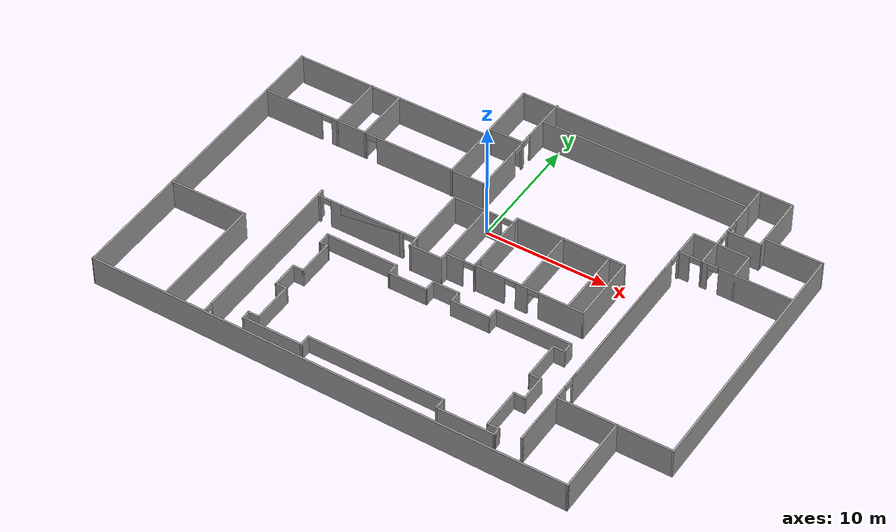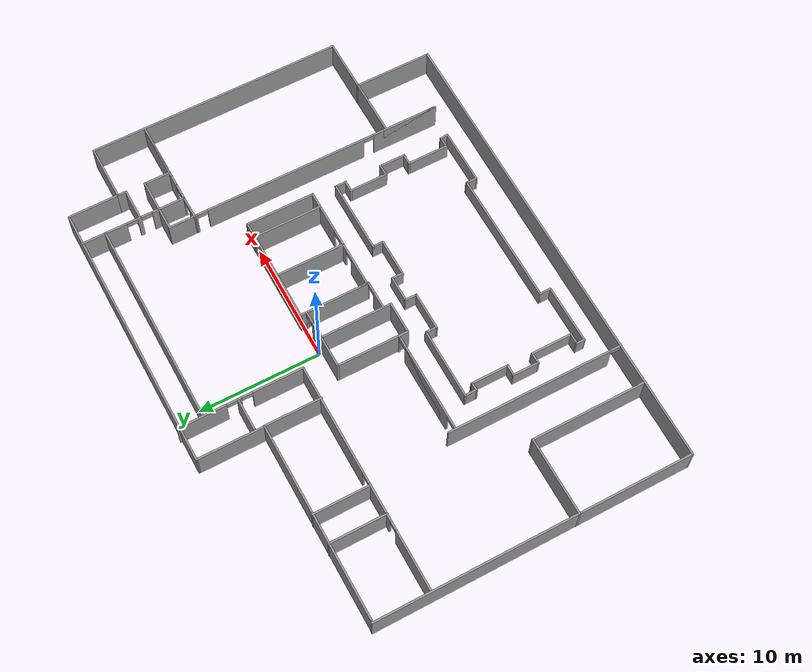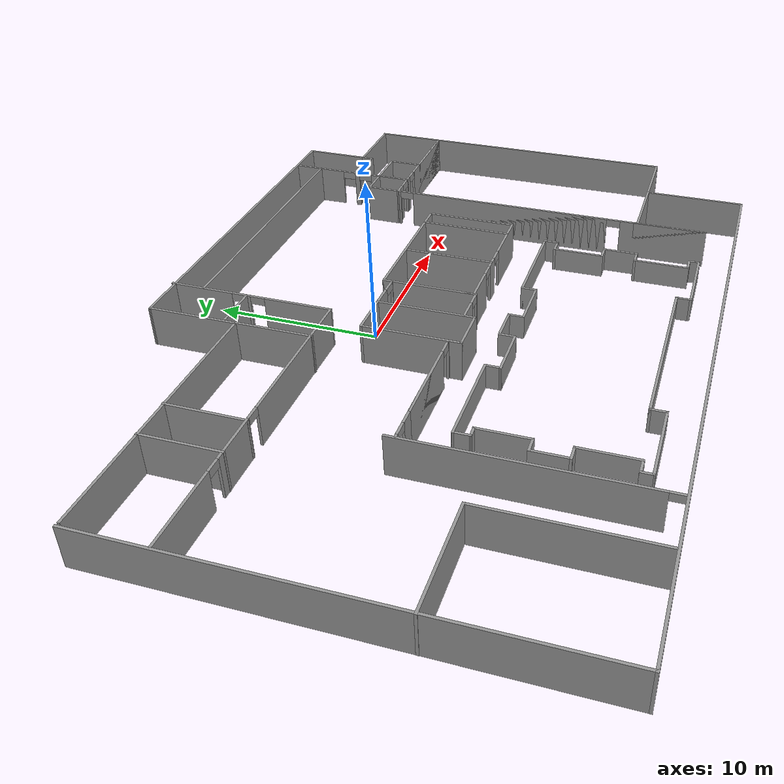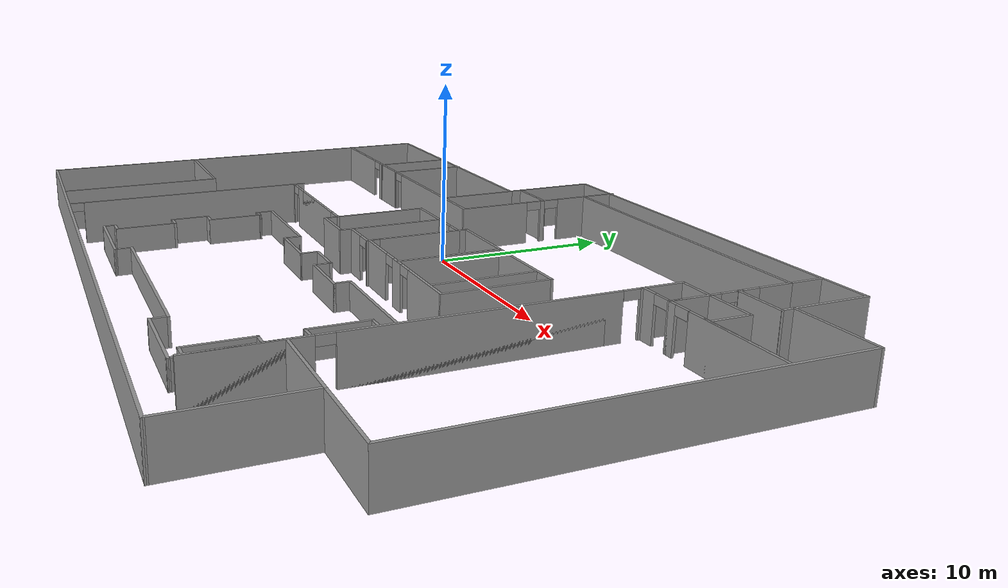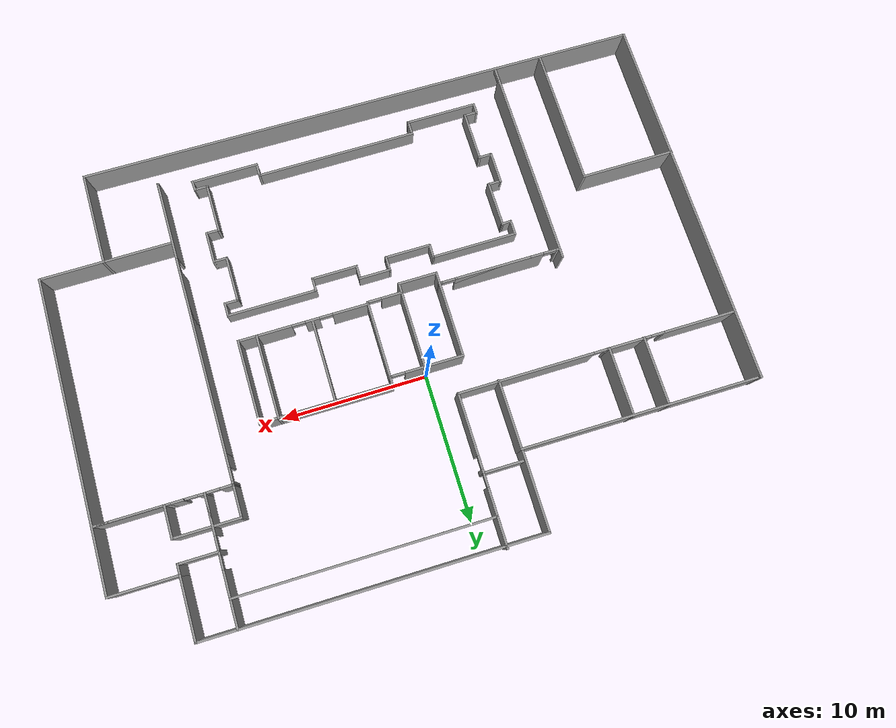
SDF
<?xml version='1.0'?>
<sdf version='1.6'>
  <model name='REPF'>
    <pose frame=''>1.1504 -3.71988 0 0 -0 0</pose>
    <link name='Wall_291'>
      <collision name='Wall_291_Collision'>
        <geometry>
          <box>
            <size>26 0.15 2.5</size>
          </box>
        </geometry>
        <pose frame=''>0 0 1.25 0 -0 0</pose>
      </collision>
      <visual name='Wall_291_Visual'>
        <pose frame=''>0 0 1.25 0 -0 0</pose>
        <geometry>
          <box>
            <size>26 0.15 2.5</size>
          </box>
        </geometry>
        <material>
          <script>
            <uri>file://media/materials/scripts/gazebo.material</uri>
            <name>Gazebo/Grey</name>
          </script>
          <ambient>1 1 1 1</ambient>
        </material>
      </visual>
      <pose frame=''>-21.7531 -2.59206 0 0 0 -1.5708</pose>
    </link>
    <link name='Wall_292'>
      <collision name='Wall_292_Collision'>
        <geometry>
          <box>
            <size>39.3304 0.15 2.5</size>
          </box>
        </geometry>
        <pose frame=''>0 0 1.25 0 -0 0</pose>
      </collision>
      <visual name='Wall_292_Visual'>
        <pose frame=''>0 0 1.25 0 -0 0</pose>
        <geometry>
          <box>
            <size>39.3304 0.15 2.5</size>
          </box>
        </geometry>
        <material>
          <script>
            <uri>file://media/materials/scripts/gazebo.material</uri>
            <name>Gazebo/Grey</name>
          </script>
          <ambient>1 1 1 1</ambient>
        </material>
      </visual>
      <pose frame=''>-2.16853 -15.6825 0 0 0 -0.008444</pose>
    </link>
    <link name='Wall_293'>
      <collision name='Wall_293_Collision'>
        <geometry>
          <box>
            <size>6.5 0.15 2.5</size>
          </box>
        </geometry>
        <pose frame=''>0 0 1.25 0 -0 0</pose>
      </collision>
      <visual name='Wall_293_Visual'>
        <pose frame=''>0 0 1.25 0 -0 0</pose>
        <geometry>
          <box>
            <size>6.5 0.15 2.5</size>
          </box>
        </geometry>
        <material>
          <script>
            <uri>file://media/materials/scripts/gazebo.material</uri>
            <name>Gazebo/Grey</name>
          </script>
          <ambient>1 1 1 1</ambient>
        </material>
      </visual>
      <pose frame=''>17.421 -12.6729 0 0 -0 1.5708</pose>
    </link>
    <link name='Wall_294'>
      <collision name='Wall_294_Collision'>
        <geometry>
          <box>
            <size>4.5 0.15 2.5</size>
          </box>
        </geometry>
        <pose frame=''>0 0 1.25 0 -0 0</pose>
      </collision>
      <visual name='Wall_294_Visual'>
        <pose frame=''>0 0 1.25 0 -0 0</pose>
        <geometry>
          <box>
            <size>4.5 0.15 2.5</size>
          </box>
        </geometry>
        <material>
          <script>
            <uri>file://media/materials/scripts/gazebo.material</uri>
            <name>Gazebo/Grey</name>
          </script>
          <ambient>1 1 1 1</ambient>
        </material>
      </visual>
      <pose frame=''>19.596 -9.49791 0 0 -0 0</pose>
    </link>
    <link name='Wall_295'>
      <collision name='Wall_295_Collision'>
        <geometry>
          <box>
            <size>21.25 0.15 2.5</size>
          </box>
        </geometry>
        <pose frame=''>0 0 1.25 0 -0 0</pose>
      </collision>
      <visual name='Wall_295_Visual'>
        <pose frame=''>0 0 1.25 0 -0 0</pose>
        <geometry>
          <box>
            <size>21.25 0.15 2.5</size>
          </box>
        </geometry>
        <material>
          <script>
            <uri>file://media/materials/scripts/gazebo.material</uri>
            <name>Gazebo/Grey</name>
          </script>
          <ambient>1 1 1 1</ambient>
        </material>
      </visual>
      <pose frame=''>21.771 1.05209 0 0 -0 1.5708</pose>
    </link>
    <link name='Wall_296'>
      <collision name='Wall_296_Collision'>
        <geometry>
          <box>
            <size>4.75 0.15 2.5</size>
          </box>
        </geometry>
        <pose frame=''>0 0 1.25 0 -0 0</pose>
      </collision>
      <visual name='Wall_296_Visual'>
        <pose frame=''>0 0 1.25 0 -0 0</pose>
        <geometry>
          <box>
            <size>4.75 0.15 2.5</size>
          </box>
        </geometry>
        <material>
          <script>
            <uri>file://media/materials/scripts/gazebo.material</uri>
            <name>Gazebo/Grey</name>
          </script>
          <ambient>1 1 1 1</ambient>
        </material>
      </visual>
      <pose frame=''>19.471 11.6021 0 0 -0 3.14159</pose>
    </link>
    <link name='Wall_297'>
      <collision name='Wall_297_Collision'>
        <geometry>
          <box>
            <size>4.25 0.15 2.5</size>
          </box>
        </geometry>
        <pose frame=''>0 0 1.25 0 -0 0</pose>
      </collision>
      <visual name='Wall_297_Visual'>
        <pose frame=''>0 0 1.25 0 -0 0</pose>
        <geometry>
          <box>
            <size>4.25 0.15 2.5</size>
          </box>
        </geometry>
        <material>
          <script>
            <uri>file://media/materials/scripts/gazebo.material</uri>
            <name>Gazebo/Grey</name>
          </script>
          <ambient>1 1 1 1</ambient>
        </material>
      </visual>
      <pose frame=''>17.171 13.6521 0 0 -0 1.5708</pose>
    </link>
    <link name='Wall_298'>
      <collision name='Wall_298_Collision'>
        <geometry>
          <box>
            <size>22.75 0.15 2.5</size>
          </box>
        </geometry>
        <pose frame=''>0 0 1.25 0 -0 0</pose>
      </collision>
      <visual name='Wall_298_Visual'>
        <pose frame=''>0 0 1.25 0 -0 0</pose>
        <geometry>
          <box>
            <size>22.75 0.15 2.5</size>
          </box>
        </geometry>
        <material>
          <script>
            <uri>file://media/materials/scripts/gazebo.material</uri>
            <name>Gazebo/Grey</name>
          </script>
          <ambient>1 1 1 1</ambient>
        </material>
      </visual>
      <pose frame=''>5.87097 15.7021 0 0 -0 3.14159</pose>
    </link>
    <link name='Wall_299'>
      <collision name='Wall_299_Collision'>
        <geometry>
          <box>
            <size>5.55237 0.15 2.5</size>
          </box>
        </geometry>
        <pose frame=''>0 0 1.25 0 -0 0</pose>
      </collision>
      <visual name='Wall_299_Visual'>
        <pose frame=''>0 0 1.25 0 -0 0</pose>
        <geometry>
          <box>
            <size>5.55237 0.15 2.5</size>
          </box>
        </geometry>
        <material>
          <script>
            <uri>file://media/materials/scripts/gazebo.material</uri>
            <name>Gazebo/Grey</name>
          </script>
          <ambient>1 1 1 1</ambient>
        </material>
      </visual>
      <pose frame=''>-5.42804 13.0009 0 0 0 -1.57043</pose>
    </link>
    <link name='Wall_300'>
      <collision name='Wall_300_Collision'>
        <geometry>
          <box>
            <size>16.25 0.15 2.5</size>
          </box>
        </geometry>
        <pose frame=''>0 0 1.25 0 -0 0</pose>
      </collision>
      <visual name='Wall_300_Visual'>
        <pose frame=''>0 0 1.25 0 -0 0</pose>
        <geometry>
          <box>
            <size>16.25 0.15 2.5</size>
          </box>
        </geometry>
        <material>
          <script>
            <uri>file://media/materials/scripts/gazebo.material</uri>
            <name>Gazebo/Grey</name>
          </script>
          <ambient>1 1 1 1</ambient>
        </material>
      </visual>
      <pose frame=''>-13.4469 10.2997 0 0 -0 3.14159</pose>
    </link>
    <link name='Wall_302'>
      <pose frame=''>-2.62455 10.7985 0 0 0 -1.5708</pose>
      <visual name='Wall_302_Visual_0'>
        <pose frame=''>-3.14213 0 1.25 0 -0 0</pose>
        <geometry>
          <box>
            <size>3.96575 0.15 2.5</size>
          </box>
        </geometry>
        <material>
          <script>
            <uri>file://media/materials/scripts/gazebo.material</uri>
            <name>Gazebo/Grey</name>
          </script>
          <ambient>1 1 1 1</ambient>
        </material>
      </visual>
      <collision name='Wall_302_Collision_0'>
        <geometry>
          <box>
            <size>3.96575 0.15 2.5</size>
          </box>
        </geometry>
        <pose frame=''>-3.14213 0 1.25 0 -0 0</pose>
      </collision>
      <visual name='Wall_302_Visual_1'>
        <pose frame=''>-0.118157 0 1.25 0 -0 0</pose>
        <geometry>
          <box>
            <size>0.282192 0.15 2.5</size>
          </box>
        </geometry>
        <material>
          <script>
            <uri>file://media/materials/scripts/gazebo.material</uri>
            <name>Gazebo/Grey</name>
          </script>
          <ambient>1 1 1 1</ambient>
        </material>
      </visual>
      <collision name='Wall_302_Collision_1'>
        <geometry>
          <box>
            <size>0.282192 0.15 2.5</size>
          </box>
        </geometry>
        <pose frame=''>-0.118157 0 1.25 0 -0 0</pose>
      </collision>
      <visual name='Wall_302_Visual_2'>
        <pose frame=''>3.02397 0 1.25 0 -0 0</pose>
        <geometry>
          <box>
            <size>4.20206 0.15 2.5</size>
          </box>
        </geometry>
        <material>
          <script>
            <uri>file://media/materials/scripts/gazebo.material</uri>
            <name>Gazebo/Grey</name>
          </script>
          <ambient>1 1 1 1</ambient>
        </material>
      </visual>
      <collision name='Wall_302_Collision_2'>
        <geometry>
          <box>
            <size>4.20206 0.15 2.5</size>
          </box>
        </geometry>
        <pose frame=''>3.02397 0 1.25 0 -0 0</pose>
      </collision>
      <visual name='Wall_302_Visual_3'>
        <pose frame=''>-0.709253 0 2.25 0 -0 0</pose>
        <geometry>
          <box>
            <size>0.9 0.15 0.5</size>
          </box>
        </geometry>
        <material>
          <script>
            <uri>file://media/materials/scripts/gazebo.material</uri>
            <name>Gazebo/Grey</name>
          </script>
          <ambient>1 1 1 1</ambient>
        </material>
      </visual>
      <collision name='Wall_302_Collision_3'>
        <geometry>
          <box>
            <size>0.9 0.15 0.5</size>
          </box>
        </geometry>
        <pose frame=''>-0.709253 0 2.25 0 -0 0</pose>
      </collision>
      <visual name='Wall_302_Visual_4'>
        <pose frame=''>0.472939 0 2.25 0 -0 0</pose>
        <geometry>
          <box>
            <size>0.9 0.15 0.5</size>
          </box>
        </geometry>
        <material>
          <script>
            <uri>file://media/materials/scripts/gazebo.material</uri>
            <name>Gazebo/Grey</name>
          </script>
          <ambient>1 1 1 1</ambient>
        </material>
      </visual>
      <collision name='Wall_302_Collision_4'>
        <geometry>
          <box>
            <size>0.9 0.15 0.5</size>
          </box>
        </geometry>
        <pose frame=''>0.472939 0 2.25 0 -0 0</pose>
      </collision>
    </link>
    <link name='Wall_303'>
      <pose frame=''>-12.1746 5.74854 0 0 -0 3.14159</pose>
      <visual name='Wall_303_Visual_0'>
        <pose frame=''>-4.94527 0 1.25 0 -0 0</pose>
        <geometry>
          <box>
            <size>9.35946 0.15 2.5</size>
          </box>
        </geometry>
        <material>
          <script>
            <uri>file://media/materials/scripts/gazebo.material</uri>
            <name>Gazebo/Grey</name>
          </script>
          <ambient>1 1 1 1</ambient>
        </material>
      </visual>
      <collision name='Wall_303_Collision_0'>
        <geometry>
          <box>
            <size>9.35946 0.15 2.5</size>
          </box>
        </geometry>
        <pose frame=''>-4.94527 0 1.25 0 -0 0</pose>
      </collision>
      <visual name='Wall_303_Visual_1'>
        <pose frame=''>2.17509 0 1.25 0 -0 0</pose>
        <geometry>
          <box>
            <size>3.08126 0.15 2.5</size>
          </box>
        </geometry>
        <material>
          <script>
            <uri>file://media/materials/scripts/gazebo.material</uri>
            <name>Gazebo/Grey</name>
          </script>
          <ambient>1 1 1 1</ambient>
        </material>
      </visual>
      <collision name='Wall_303_Collision_1'>
        <geometry>
          <box>
            <size>3.08126 0.15 2.5</size>
          </box>
        </geometry>
        <pose frame=''>2.17509 0 1.25 0 -0 0</pose>
      </collision>
      <visual name='Wall_303_Visual_2'>
        <pose frame=''>7.12036 0 1.25 0 -0 0</pose>
        <geometry>
          <box>
            <size>5.00928 0.15 2.5</size>
          </box>
        </geometry>
        <material>
          <script>
            <uri>file://media/materials/scripts/gazebo.material</uri>
            <name>Gazebo/Grey</name>
          </script>
          <ambient>1 1 1 1</ambient>
        </material>
      </visual>
      <collision name='Wall_303_Collision_2'>
        <geometry>
          <box>
            <size>5.00928 0.15 2.5</size>
          </box>
        </geometry>
        <pose frame=''>7.12036 0 1.25 0 -0 0</pose>
      </collision>
      <visual name='Wall_303_Visual_3'>
        <pose frame=''>0.18446 0 2.25 0 -0 0</pose>
        <geometry>
          <box>
            <size>0.9 0.15 0.5</size>
          </box>
        </geometry>
        <material>
          <script>
            <uri>file://media/materials/scripts/gazebo.material</uri>
            <name>Gazebo/Grey</name>
          </script>
          <ambient>1 1 1 1</ambient>
        </material>
      </visual>
      <collision name='Wall_303_Collision_3'>
        <geometry>
          <box>
            <size>0.9 0.15 0.5</size>
          </box>
        </geometry>
        <pose frame=''>0.18446 0 2.25 0 -0 0</pose>
      </collision>
      <visual name='Wall_303_Visual_4'>
        <pose frame=''>4.16572 0 2.25 0 -0 0</pose>
        <geometry>
          <box>
            <size>0.9 0.15 0.5</size>
          </box>
        </geometry>
        <material>
          <script>
            <uri>file://media/materials/scripts/gazebo.material</uri>
            <name>Gazebo/Grey</name>
          </script>
          <ambient>1 1 1 1</ambient>
        </material>
      </visual>
      <collision name='Wall_303_Collision_4'>
        <geometry>
          <box>
            <size>0.9 0.15 0.5</size>
          </box>
        </geometry>
        <pose frame=''>4.16572 0 2.25 0 -0 0</pose>
      </collision>
    </link>
    <link name='Wall_305'>
      <collision name='Wall_305_Collision'>
        <geometry>
          <box>
            <size>4.75 0.15 2.5</size>
          </box>
        </geometry>
        <pose frame=''>0 0 1.25 0 -0 0</pose>
      </collision>
      <visual name='Wall_305_Visual'>
        <pose frame=''>0 0 1.25 0 -0 0</pose>
        <geometry>
          <box>
            <size>4.75 0.15 2.5</size>
          </box>
        </geometry>
        <material>
          <script>
            <uri>file://media/materials/scripts/gazebo.material</uri>
            <name>Gazebo/Grey</name>
          </script>
          <ambient>1 1 1 1</ambient>
        </material>
      </visual>
      <pose frame=''>-5.39685 7.99971 0 0 0 -1.5708</pose>
    </link>
    <link name='Wall_307'>
      <collision name='Wall_307_Collision'>
        <geometry>
          <box>
            <size>2.75 0.15 2.5</size>
          </box>
        </geometry>
        <pose frame=''>0 0 1.25 0 -0 0</pose>
      </collision>
      <visual name='Wall_307_Visual'>
        <pose frame=''>0 0 1.25 0 -0 0</pose>
        <geometry>
          <box>
            <size>2.75 0.15 2.5</size>
          </box>
        </geometry>
        <material>
          <script>
            <uri>file://media/materials/scripts/gazebo.material</uri>
            <name>Gazebo/Grey</name>
          </script>
          <ambient>1 1 1 1</ambient>
        </material>
      </visual>
      <pose frame=''>-3.94634 11.0349 0 0 -0 0</pose>
    </link>
    <link name='Wall_309'>
      <collision name='Wall_309_Collision'>
        <geometry>
          <box>
            <size>17.25 0.15 2.5</size>
          </box>
        </geometry>
        <pose frame=''>0 0 1.25 0 -0 0</pose>
      </collision>
      <visual name='Wall_309_Visual'>
        <pose frame=''>0 0 1.25 0 -0 0</pose>
        <geometry>
          <box>
            <size>17.25 0.15 2.5</size>
          </box>
        </geometry>
        <material>
          <script>
            <uri>file://media/materials/scripts/gazebo.material</uri>
            <name>Gazebo/Grey</name>
          </script>
          <ambient>1 1 1 1</ambient>
        </material>
      </visual>
      <pose frame=''>5.99398 13.832 0 0 -0 0</pose>
    </link>
    <link name='Wall_310'>
      <collision name='Wall_310_Collision'>
        <geometry>
          <box>
            <size>2 0.15 2.5</size>
          </box>
        </geometry>
        <pose frame=''>0 0 1.25 0 -0 0</pose>
      </collision>
      <visual name='Wall_310_Visual'>
        <pose frame=''>0 0 1.25 0 -0 0</pose>
        <geometry>
          <box>
            <size>2 0.15 2.5</size>
          </box>
        </geometry>
        <material>
          <script>
            <uri>file://media/materials/scripts/gazebo.material</uri>
            <name>Gazebo/Grey</name>
          </script>
          <ambient>1 1 1 1</ambient>
        </material>
      </visual>
      <pose frame=''>14.544 14.757 0 0 -0 1.5708</pose>
    </link>
    <link name='Wall_312'>
      <pose frame=''>14.544 10.532 0 0 0 -1.5708</pose>
      <visual name='Wall_312_Visual_0'>
        <pose frame=''>-2.44988 0 1.25 0 -0 0</pose>
        <geometry>
          <box>
            <size>1.85025 0.15 2.5</size>
          </box>
        </geometry>
        <material>
          <script>
            <uri>file://media/materials/scripts/gazebo.material</uri>
            <name>Gazebo/Grey</name>
          </script>
          <ambient>1 1 1 1</ambient>
        </material>
      </visual>
      <collision name='Wall_312_Collision_0'>
        <geometry>
          <box>
            <size>1.85025 0.15 2.5</size>
          </box>
        </geometry>
        <pose frame=''>-2.44988 0 1.25 0 -0 0</pose>
      </collision>
      <visual name='Wall_312_Visual_1'>
        <pose frame=''>-0.462424 0 1.25 0 -0 0</pose>
        <geometry>
          <box>
            <size>0.324652 0.15 2.5</size>
          </box>
        </geometry>
        <material>
          <script>
            <uri>file://media/materials/scripts/gazebo.material</uri>
            <name>Gazebo/Grey</name>
          </script>
          <ambient>1 1 1 1</ambient>
        </material>
      </visual>
      <collision name='Wall_312_Collision_1'>
        <geometry>
          <box>
            <size>0.324652 0.15 2.5</size>
          </box>
        </geometry>
        <pose frame=''>-0.462424 0 1.25 0 -0 0</pose>
      </collision>
      <visual name='Wall_312_Visual_2'>
        <pose frame=''>1.98745 0 1.25 0 -0 0</pose>
        <geometry>
          <box>
            <size>2.7751 0.15 2.5</size>
          </box>
        </geometry>
        <material>
          <script>
            <uri>file://media/materials/scripts/gazebo.material</uri>
            <name>Gazebo/Grey</name>
          </script>
          <ambient>1 1 1 1</ambient>
        </material>
      </visual>
      <collision name='Wall_312_Collision_2'>
        <geometry>
          <box>
            <size>2.7751 0.15 2.5</size>
          </box>
        </geometry>
        <pose frame=''>1.98745 0 1.25 0 -0 0</pose>
      </collision>
      <visual name='Wall_312_Visual_3'>
        <pose frame=''>-1.07475 0 2.25 0 -0 0</pose>
        <geometry>
          <box>
            <size>0.9 0.15 0.5</size>
          </box>
        </geometry>
        <material>
          <script>
            <uri>file://media/materials/scripts/gazebo.material</uri>
            <name>Gazebo/Grey</name>
          </script>
          <ambient>1 1 1 1</ambient>
        </material>
      </visual>
      <collision name='Wall_312_Collision_3'>
        <geometry>
          <box>
            <size>0.9 0.15 0.5</size>
          </box>
        </geometry>
        <pose frame=''>-1.07475 0 2.25 0 -0 0</pose>
      </collision>
      <visual name='Wall_312_Visual_4'>
        <pose frame=''>0.149902 0 2.25 0 -0 0</pose>
        <geometry>
          <box>
            <size>0.9 0.15 0.5</size>
          </box>
        </geometry>
        <material>
          <script>
            <uri>file://media/materials/scripts/gazebo.material</uri>
            <name>Gazebo/Grey</name>
          </script>
          <ambient>1 1 1 1</ambient>
        </material>
      </visual>
      <collision name='Wall_312_Collision_4'>
        <geometry>
          <box>
            <size>0.9 0.15 0.5</size>
          </box>
        </geometry>
        <pose frame=''>0.149902 0 2.25 0 -0 0</pose>
      </collision>
    </link>
    <link name='Wall_313'>
      <pose frame=''>13.619 7.22222 0 0 0 -3.13104</pose>
      <visual name='Wall_313_Visual_0'>
        <pose frame=''>-0.91553 0 1.25 0 -0 0</pose>
        <geometry>
          <box>
            <size>0.168939 0.15 2.5</size>
          </box>
        </geometry>
        <material>
          <script>
            <uri>file://media/materials/scripts/gazebo.material</uri>
            <name>Gazebo/Grey</name>
          </script>
          <ambient>1 1 1 1</ambient>
        </material>
      </visual>
      <collision name='Wall_313_Collision_0'>
        <geometry>
          <box>
            <size>0.168939 0.15 2.5</size>
          </box>
        </geometry>
        <pose frame=''>-0.91553 0 1.25 0 -0 0</pose>
      </collision>
      <visual name='Wall_313_Visual_1'>
        <pose frame=''>0.53447 0 1.25 0 -0 0</pose>
        <geometry>
          <box>
            <size>0.931061 0.15 2.5</size>
          </box>
        </geometry>
        <material>
          <script>
            <uri>file://media/materials/scripts/gazebo.material</uri>
            <name>Gazebo/Grey</name>
          </script>
          <ambient>1 1 1 1</ambient>
        </material>
      </visual>
      <collision name='Wall_313_Collision_1'>
        <geometry>
          <box>
            <size>0.931061 0.15 2.5</size>
          </box>
        </geometry>
        <pose frame=''>0.53447 0 1.25 0 -0 0</pose>
      </collision>
      <visual name='Wall_313_Visual_2'>
        <pose frame=''>-0.381061 0 2.25 0 -0 0</pose>
        <geometry>
          <box>
            <size>0.9 0.15 0.5</size>
          </box>
        </geometry>
        <material>
          <script>
            <uri>file://media/materials/scripts/gazebo.material</uri>
            <name>Gazebo/Grey</name>
          </script>
          <ambient>1 1 1 1</ambient>
        </material>
      </visual>
      <collision name='Wall_313_Collision_2'>
        <geometry>
          <box>
            <size>0.9 0.15 0.5</size>
          </box>
        </geometry>
        <pose frame=''>-0.381061 0 2.25 0 -0 0</pose>
      </collision>
    </link>
    <link name='Wall_314'>
      <collision name='Wall_314_Collision'>
        <geometry>
          <box>
            <size>2.26953 0.15 2.5</size>
          </box>
        </geometry>
        <pose frame=''>0 0 1.25 0 -0 0</pose>
      </collision>
      <visual name='Wall_314_Visual'>
        <pose frame=''>0 0 1.25 0 -0 0</pose>
        <geometry>
          <box>
            <size>2.26953 0.15 2.5</size>
          </box>
        </geometry>
        <material>
          <script>
            <uri>file://media/materials/scripts/gazebo.material</uri>
            <name>Gazebo/Grey</name>
          </script>
          <ambient>1 1 1 1</ambient>
        </material>
      </visual>
      <pose frame=''>12.694 8.27222 0 0 -0 1.5708</pose>
    </link>
    <link name='Wall_315'>
      <collision name='Wall_315_Collision'>
        <geometry>
          <box>
            <size>2 0.15 2.5</size>
          </box>
        </geometry>
        <pose frame=''>0 0 1.25 0 -0 0</pose>
      </collision>
      <visual name='Wall_315_Visual'>
        <pose frame=''>0 0 1.25 0 -0 0</pose>
        <geometry>
          <box>
            <size>2 0.15 2.5</size>
          </box>
        </geometry>
        <material>
          <script>
            <uri>file://media/materials/scripts/gazebo.material</uri>
            <name>Gazebo/Grey</name>
          </script>
          <ambient>1 1 1 1</ambient>
        </material>
      </visual>
      <pose frame=''>13.619 9.33198 0 0 -0 0</pose>
    </link>
    <link name='Wall_317'>
      <collision name='Wall_317_Collision'>
        <geometry>
          <box>
            <size>2.75 0.15 2.5</size>
          </box>
        </geometry>
        <pose frame=''>0 0 1.25 0 -0 0</pose>
      </collision>
      <visual name='Wall_317_Visual'>
        <pose frame=''>0 0 1.25 0 -0 0</pose>
        <geometry>
          <box>
            <size>2.75 0.15 2.5</size>
          </box>
        </geometry>
        <material>
          <script>
            <uri>file://media/materials/scripts/gazebo.material</uri>
            <name>Gazebo/Grey</name>
          </script>
          <ambient>1 1 1 1</ambient>
        </material>
      </visual>
      <pose frame=''>15.8713 10.9244 0 0 -0 0</pose>
    </link>
    <link name='Wall_318'>
      <collision name='Wall_318_Collision'>
        <geometry>
          <box>
            <size>0.827663 0.15 2.5</size>
          </box>
        </geometry>
        <pose frame=''>0 0 1.25 0 -0 0</pose>
      </collision>
      <visual name='Wall_318_Visual'>
        <pose frame=''>0 0 1.25 0 -0 0</pose>
        <geometry>
          <box>
            <size>0.827663 0.15 2.5</size>
          </box>
        </geometry>
        <material>
          <script>
            <uri>file://media/materials/scripts/gazebo.material</uri>
            <name>Gazebo/Grey</name>
          </script>
          <ambient>1 1 1 1</ambient>
        </material>
      </visual>
      <pose frame=''>17.1711 11.2633 0 0 -0 1.57131</pose>
    </link>
    <link name='Wall_320'>
      <collision name='Wall_320_Collision'>
        <geometry>
          <box>
            <size>2.25 0.15 2.5</size>
          </box>
        </geometry>
        <pose frame=''>0 0 1.25 0 -0 0</pose>
      </collision>
      <visual name='Wall_320_Visual'>
        <pose frame=''>0 0 1.25 0 -0 0</pose>
        <geometry>
          <box>
            <size>2.25 0.15 2.5</size>
          </box>
        </geometry>
        <material>
          <script>
            <uri>file://media/materials/scripts/gazebo.material</uri>
            <name>Gazebo/Grey</name>
          </script>
          <ambient>1 1 1 1</ambient>
        </material>
      </visual>
      <pose frame=''>14.544 8.28198 0 0 0 -1.5708</pose>
    </link>
    <link name='Wall_321'>
      <pose frame=''>18.094 7.23198 0 0 -0 0</pose>
      <visual name='Wall_321_Visual_0'>
        <pose frame=''>-3.36352 0 1.25 0 -0 0</pose>
        <geometry>
          <box>
            <size>0.522969 0.15 2.5</size>
          </box>
        </geometry>
        <material>
          <script>
            <uri>file://media/materials/scripts/gazebo.material</uri>
            <name>Gazebo/Grey</name>
          </script>
          <ambient>1 1 1 1</ambient>
        </material>
      </visual>
      <collision name='Wall_321_Collision_0'>
        <geometry>
          <box>
            <size>0.522969 0.15 2.5</size>
          </box>
        </geometry>
        <pose frame=''>-3.36352 0 1.25 0 -0 0</pose>
      </collision>
      <visual name='Wall_321_Visual_1'>
        <pose frame=''>0.711485 0 1.25 0 -0 0</pose>
        <geometry>
          <box>
            <size>5.82703 0.15 2.5</size>
          </box>
        </geometry>
        <material>
          <script>
            <uri>file://media/materials/scripts/gazebo.material</uri>
            <name>Gazebo/Grey</name>
          </script>
          <ambient>1 1 1 1</ambient>
        </material>
      </visual>
      <collision name='Wall_321_Collision_1'>
        <geometry>
          <box>
            <size>5.82703 0.15 2.5</size>
          </box>
        </geometry>
        <pose frame=''>0.711485 0 1.25 0 -0 0</pose>
      </collision>
      <visual name='Wall_321_Visual_2'>
        <pose frame=''>1.13616 0 1.25 0 -0 0</pose>
        <geometry>
          <box>
            <size>4.97768 0.15 2.5</size>
          </box>
        </geometry>
        <material>
          <script>
            <uri>file://media/materials/scripts/gazebo.material</uri>
            <name>Gazebo/Grey</name>
          </script>
          <ambient>1 1 1 1</ambient>
        </material>
      </visual>
      <collision name='Wall_321_Collision_2'>
        <geometry>
          <box>
            <size>4.97768 0.15 2.5</size>
          </box>
        </geometry>
        <pose frame=''>1.13616 0 1.25 0 -0 0</pose>
      </collision>
      <visual name='Wall_321_Visual_3'>
        <pose frame=''>-2.67735 0 2.25 0 -0 0</pose>
        <geometry>
          <box>
            <size>0.849354 0.15 0.5</size>
          </box>
        </geometry>
        <material>
          <script>
            <uri>file://media/materials/scripts/gazebo.material</uri>
            <name>Gazebo/Grey</name>
          </script>
          <ambient>1 1 1 1</ambient>
        </material>
      </visual>
      <collision name='Wall_321_Collision_3'>
        <geometry>
          <box>
            <size>0.849354 0.15 0.5</size>
          </box>
        </geometry>
        <pose frame=''>-2.67735 0 2.25 0 -0 0</pose>
      </collision>
    </link>
    <link name='Wall_323'>
      <collision name='Wall_323_Collision'>
        <geometry>
          <box>
            <size>2.75 0.15 2.5</size>
          </box>
        </geometry>
        <pose frame=''>0 0 1.25 0 -0 0</pose>
      </collision>
      <visual name='Wall_323_Visual'>
        <pose frame=''>0 0 1.25 0 -0 0</pose>
        <geometry>
          <box>
            <size>2.75 0.15 2.5</size>
          </box>
        </geometry>
        <material>
          <script>
            <uri>file://media/materials/scripts/gazebo.material</uri>
            <name>Gazebo/Grey</name>
          </script>
          <ambient>1 1 1 1</ambient>
        </material>
      </visual>
      <pose frame=''>15.844 9.33198 0 0 -0 0</pose>
    </link>
    <link name='Wall_324'>
      <collision name='Wall_324_Collision'>
        <geometry>
          <box>
            <size>2.25 0.15 2.5</size>
          </box>
        </geometry>
        <pose frame=''>0 0 1.25 0 -0 0</pose>
      </collision>
      <visual name='Wall_324_Visual'>
        <pose frame=''>0 0 1.25 0 -0 0</pose>
        <geometry>
          <box>
            <size>2.25 0.15 2.5</size>
          </box>
        </geometry>
        <material>
          <script>
            <uri>file://media/materials/scripts/gazebo.material</uri>
            <name>Gazebo/Grey</name>
          </script>
          <ambient>1 1 1 1</ambient>
        </material>
      </visual>
      <pose frame=''>17.144 8.28198 0 0 0 -1.5708</pose>
    </link>
    <link name='Wall_327'>
      <pose frame=''>12.694 -3.32778 0 0 0 -1.5708</pose>
      <visual name='Wall_327_Visual_0'>
        <pose frame=''>-10.4755 0 1.25 0 -0 0</pose>
        <geometry>
          <box>
            <size>0.29897 0.15 2.5</size>
          </box>
        </geometry>
        <material>
          <script>
            <uri>file://media/materials/scripts/gazebo.material</uri>
            <name>Gazebo/Grey</name>
          </script>
          <ambient>1 1 1 1</ambient>
        </material>
      </visual>
      <collision name='Wall_327_Collision_0'>
        <geometry>
          <box>
            <size>0.29897 0.15 2.5</size>
          </box>
        </geometry>
        <pose frame=''>-10.4755 0 1.25 0 -0 0</pose>
      </collision>
      <visual name='Wall_327_Visual_1'>
        <pose frame=''>-2.64993 0 1.25 0 -0 0</pose>
        <geometry>
          <box>
            <size>13.5522 0.15 2.5</size>
          </box>
        </geometry>
        <material>
          <script>
            <uri>file://media/materials/scripts/gazebo.material</uri>
            <name>Gazebo/Grey</name>
          </script>
          <ambient>1 1 1 1</ambient>
        </material>
      </visual>
      <collision name='Wall_327_Collision_1'>
        <geometry>
          <box>
            <size>13.5522 0.15 2.5</size>
          </box>
        </geometry>
        <pose frame=''>-2.64993 0 1.25 0 -0 0</pose>
      </collision>
      <visual name='Wall_327_Visual_2'>
        <pose frame=''>-2.20373 0 1.25 0 -0 0</pose>
        <geometry>
          <box>
            <size>12.6598 0.15 2.5</size>
          </box>
        </geometry>
        <material>
          <script>
            <uri>file://media/materials/scripts/gazebo.material</uri>
            <name>Gazebo/Grey</name>
          </script>
          <ambient>1 1 1 1</ambient>
        </material>
      </visual>
      <collision name='Wall_327_Collision_2'>
        <geometry>
          <box>
            <size>12.6598 0.15 2.5</size>
          </box>
        </geometry>
        <pose frame=''>-2.20373 0 1.25 0 -0 0</pose>
      </collision>
      <visual name='Wall_327_Visual_3'>
        <pose frame=''>7.82559 0 1.25 0 -0 0</pose>
        <geometry>
          <box>
            <size>5.59883 0.15 2.5</size>
          </box>
        </geometry>
        <material>
          <script>
            <uri>file://media/materials/scripts/gazebo.material</uri>
            <name>Gazebo/Grey</name>
          </script>
          <ambient>1 1 1 1</ambient>
        </material>
      </visual>
      <collision name='Wall_327_Collision_3'>
        <geometry>
          <box>
            <size>5.59883 0.15 2.5</size>
          </box>
        </geometry>
        <pose frame=''>7.82559 0 1.25 0 -0 0</pose>
      </collision>
      <visual name='Wall_327_Visual_4'>
        <pose frame=''>8.27478 0 1.25 0 -0 0</pose>
        <geometry>
          <box>
            <size>4.70045 0.15 2.5</size>
          </box>
        </geometry>
        <material>
          <script>
            <uri>file://media/materials/scripts/gazebo.material</uri>
            <name>Gazebo/Grey</name>
          </script>
          <ambient>1 1 1 1</ambient>
        </material>
      </visual>
      <collision name='Wall_327_Collision_4'>
        <geometry>
          <box>
            <size>4.70045 0.15 2.5</size>
          </box>
        </geometry>
        <pose frame=''>8.27478 0 1.25 0 -0 0</pose>
      </collision>
      <visual name='Wall_327_Visual_5'>
        <pose frame=''>-9.87983 0 2.25 0 -0 0</pose>
        <geometry>
          <box>
            <size>0.892405 0.15 0.5</size>
          </box>
        </geometry>
        <material>
          <script>
            <uri>file://media/materials/scripts/gazebo.material</uri>
            <name>Gazebo/Grey</name>
          </script>
          <ambient>1 1 1 1</ambient>
        </material>
      </visual>
      <collision name='Wall_327_Collision_5'>
        <geometry>
          <box>
            <size>0.892405 0.15 0.5</size>
          </box>
        </geometry>
        <pose frame=''>-9.87983 0 2.25 0 -0 0</pose>
      </collision>
      <visual name='Wall_327_Visual_6'>
        <pose frame=''>4.57536 0 2.25 0 -0 0</pose>
        <geometry>
          <box>
            <size>0.89838 0.15 0.5</size>
          </box>
        </geometry>
        <material>
          <script>
            <uri>file://media/materials/scripts/gazebo.material</uri>
            <name>Gazebo/Grey</name>
          </script>
          <ambient>1 1 1 1</ambient>
        </material>
      </visual>
      <collision name='Wall_327_Collision_6'>
        <geometry>
          <box>
            <size>0.89838 0.15 0.5</size>
          </box>
        </geometry>
        <pose frame=''>4.57536 0 2.25 0 -0 0</pose>
      </collision>
      <visual name='Wall_327_Visual_7'>
        <pose frame=''>4.57536 0 2.25 0 -0 0</pose>
        <geometry>
          <box>
            <size>0.89838 0.15 0.5</size>
          </box>
        </geometry>
        <material>
          <script>
            <uri>file://media/materials/scripts/gazebo.material</uri>
            <name>Gazebo/Grey</name>
          </script>
          <ambient>1 1 1 1</ambient>
        </material>
      </visual>
      <collision name='Wall_327_Collision_7'>
        <geometry>
          <box>
            <size>0.89838 0.15 0.5</size>
          </box>
        </geometry>
        <pose frame=''>4.57536 0 2.25 0 -0 0</pose>
      </collision>
    </link>
    <link name='Wall_329'>
      <collision name='Wall_329_Collision'>
        <geometry>
          <box>
            <size>4.75 0.15 2.5</size>
          </box>
        </geometry>
        <pose frame=''>0 0 1.25 0 -0 0</pose>
      </collision>
      <visual name='Wall_329_Visual'>
        <pose frame=''>0 0 1.25 0 -0 0</pose>
        <geometry>
          <box>
            <size>4.75 0.15 2.5</size>
          </box>
        </geometry>
        <material>
          <script>
            <uri>file://media/materials/scripts/gazebo.material</uri>
            <name>Gazebo/Grey</name>
          </script>
          <ambient>1 1 1 1</ambient>
        </material>
      </visual>
      <pose frame=''>15.121 -9.49791 0 0 -0 3.14159</pose>
    </link>
    <link name='Wall_331'>
      <collision name='Wall_331_Collision'>
        <geometry>
          <box>
            <size>6.5 0.15 2.5</size>
          </box>
        </geometry>
        <pose frame=''>0 0 1.25 0 -0 0</pose>
      </collision>
      <visual name='Wall_331_Visual'>
        <pose frame=''>0 0 1.25 0 -0 0</pose>
        <geometry>
          <box>
            <size>6.5 0.15 2.5</size>
          </box>
        </geometry>
        <material>
          <script>
            <uri>file://media/materials/scripts/gazebo.material</uri>
            <name>Gazebo/Grey</name>
          </script>
          <ambient>1 1 1 1</ambient>
        </material>
      </visual>
      <pose frame=''>-18.596 -6.09631 0 0 -0 0</pose>
    </link>
    <link name='Wall_332'>
      <collision name='Wall_332_Collision'>
        <geometry>
          <box>
            <size>9.5 0.15 2.5</size>
          </box>
        </geometry>
        <pose frame=''>0 0 1.25 0 -0 0</pose>
      </collision>
      <visual name='Wall_332_Visual'>
        <pose frame=''>0 0 1.25 0 -0 0</pose>
        <geometry>
          <box>
            <size>9.5 0.15 2.5</size>
          </box>
        </geometry>
        <material>
          <script>
            <uri>file://media/materials/scripts/gazebo.material</uri>
            <name>Gazebo/Grey</name>
          </script>
          <ambient>1 1 1 1</ambient>
        </material>
      </visual>
      <pose frame=''>-15.421 -10.7713 0 0 0 -1.5708</pose>
    </link>
    <link name='Wall_334'>
      <pose frame=''>-12.1022 -8.27314 0 0 0 -1.5708</pose>
      <visual name='Wall_334_Visual_0'>
        <pose frame=''>-0.398977 0 1.25 0 -0 0</pose>
        <geometry>
          <box>
            <size>13.702 0.15 2.5</size>
          </box>
        </geometry>
        <material>
          <script>
            <uri>file://media/materials/scripts/gazebo.material</uri>
            <name>Gazebo/Grey</name>
          </script>
          <ambient>1 1 1 1</ambient>
        </material>
      </visual>
      <collision name='Wall_334_Collision_0'>
        <geometry>
          <box>
            <size>13.702 0.15 2.5</size>
          </box>
        </geometry>
        <pose frame=''>-0.398977 0 1.25 0 -0 0</pose>
      </collision>
      <visual name='Wall_334_Visual_1'>
        <pose frame=''>6.85102 0 2.25 0 -0 0</pose>
        <geometry>
          <box>
            <size>0.797955 0.15 0.5</size>
          </box>
        </geometry>
        <material>
          <script>
            <uri>file://media/materials/scripts/gazebo.material</uri>
            <name>Gazebo/Grey</name>
          </script>
          <ambient>1 1 1 1</ambient>
        </material>
      </visual>
      <collision name='Wall_334_Collision_1'>
        <geometry>
          <box>
            <size>0.797955 0.15 0.5</size>
          </box>
        </geometry>
        <pose frame=''>6.85102 0 2.25 0 -0 0</pose>
      </collision>
    </link>
    <link name='Wall_336'>
      <pose frame=''>-7.83845 -1.65312 0 0 -0 0</pose>
      <visual name='Wall_336_Visual_0'>
        <pose frame=''>-4.13254 0 1.25 0 -0 0</pose>
        <geometry>
          <box>
            <size>0.234928 0.15 2.5</size>
          </box>
        </geometry>
        <material>
          <script>
            <uri>file://media/materials/scripts/gazebo.material</uri>
            <name>Gazebo/Grey</name>
          </script>
          <ambient>1 1 1 1</ambient>
        </material>
      </visual>
      <collision name='Wall_336_Collision_0'>
        <geometry>
          <box>
            <size>0.234928 0.15 2.5</size>
          </box>
        </geometry>
        <pose frame=''>-4.13254 0 1.25 0 -0 0</pose>
      </collision>
      <visual name='Wall_336_Visual_1'>
        <pose frame=''>-0.006322 0 1.25 0 -0 0</pose>
        <geometry>
          <box>
            <size>6.2175 0.15 2.5</size>
          </box>
        </geometry>
        <material>
          <script>
            <uri>file://media/materials/scripts/gazebo.material</uri>
            <name>Gazebo/Grey</name>
          </script>
          <ambient>1 1 1 1</ambient>
        </material>
      </visual>
      <collision name='Wall_336_Collision_1'>
        <geometry>
          <box>
            <size>6.2175 0.15 2.5</size>
          </box>
        </geometry>
        <pose frame=''>-0.006322 0 1.25 0 -0 0</pose>
      </collision>
      <visual name='Wall_336_Visual_2'>
        <pose frame=''>0.440485 0 1.25 0 -0 0</pose>
        <geometry>
          <box>
            <size>5.32388 0.15 2.5</size>
          </box>
        </geometry>
        <material>
          <script>
            <uri>file://media/materials/scripts/gazebo.material</uri>
            <name>Gazebo/Grey</name>
          </script>
          <ambient>1 1 1 1</ambient>
        </material>
      </visual>
      <collision name='Wall_336_Collision_2'>
        <geometry>
          <box>
            <size>5.32388 0.15 2.5</size>
          </box>
        </geometry>
        <pose frame=''>0.440485 0 1.25 0 -0 0</pose>
      </collision>
      <visual name='Wall_336_Visual_3'>
        <pose frame=''>4.12621 0 1.25 0 -0 0</pose>
        <geometry>
          <box>
            <size>0.247573 0.15 2.5</size>
          </box>
        </geometry>
        <material>
          <script>
            <uri>file://media/materials/scripts/gazebo.material</uri>
            <name>Gazebo/Grey</name>
          </script>
          <ambient>1 1 1 1</ambient>
        </material>
      </visual>
      <collision name='Wall_336_Collision_3'>
        <geometry>
          <box>
            <size>0.247573 0.15 2.5</size>
          </box>
        </geometry>
        <pose frame=''>4.12621 0 1.25 0 -0 0</pose>
      </collision>
      <visual name='Wall_336_Visual_4'>
        <pose frame=''>-3.56826 0 2.25 0 -0 0</pose>
        <geometry>
          <box>
            <size>0.893616 0.15 0.5</size>
          </box>
        </geometry>
        <material>
          <script>
            <uri>file://media/materials/scripts/gazebo.material</uri>
            <name>Gazebo/Grey</name>
          </script>
          <ambient>1 1 1 1</ambient>
        </material>
      </visual>
      <collision name='Wall_336_Collision_4'>
        <geometry>
          <box>
            <size>0.893616 0.15 0.5</size>
          </box>
        </geometry>
        <pose frame=''>-3.56826 0 2.25 0 -0 0</pose>
      </collision>
      <visual name='Wall_336_Visual_5'>
        <pose frame=''>3.55243 0 2.25 0 -0 0</pose>
        <geometry>
          <box>
            <size>0.9 0.15 0.5</size>
          </box>
        </geometry>
        <material>
          <script>
            <uri>file://media/materials/scripts/gazebo.material</uri>
            <name>Gazebo/Grey</name>
          </script>
          <ambient>1 1 1 1</ambient>
        </material>
      </visual>
      <collision name='Wall_336_Collision_5'>
        <geometry>
          <box>
            <size>0.9 0.15 0.5</size>
          </box>
        </geometry>
        <pose frame=''>3.55243 0 2.25 0 -0 0</pose>
      </collision>
      <visual name='Wall_336_Visual_6'>
        <pose frame=''>3.55243 0 2.25 0 -0 0</pose>
        <geometry>
          <box>
            <size>0.9 0.15 0.5</size>
          </box>
        </geometry>
        <material>
          <script>
            <uri>file://media/materials/scripts/gazebo.material</uri>
            <name>Gazebo/Grey</name>
          </script>
          <ambient>1 1 1 1</ambient>
        </material>
      </visual>
      <collision name='Wall_336_Collision_6'>
        <geometry>
          <box>
            <size>0.9 0.15 0.5</size>
          </box>
        </geometry>
        <pose frame=''>3.55243 0 2.25 0 -0 0</pose>
      </collision>
    </link>
    <link name='Wall_338'>
      <collision name='Wall_338_Collision'>
        <geometry>
          <box>
            <size>6 0.15 2.5</size>
          </box>
        </geometry>
        <pose frame=''>0 0 1.25 0 -0 0</pose>
      </collision>
      <visual name='Wall_338_Visual'>
        <pose frame=''>0 0 1.25 0 -0 0</pose>
        <geometry>
          <box>
            <size>6 0.15 2.5</size>
          </box>
        </geometry>
        <material>
          <script>
            <uri>file://media/materials/scripts/gazebo.material</uri>
            <name>Gazebo/Grey</name>
          </script>
          <ambient>1 1 1 1</ambient>
        </material>
      </visual>
      <pose frame=''>-3.6668 0.527981 0 0 0 -1.5708</pose>
    </link>
    <link name='Wall_339'>
      <collision name='Wall_339_Collision'>
        <geometry>
          <box>
            <size>2.75 0.15 2.5</size>
          </box>
        </geometry>
        <pose frame=''>0 0 1.25 0 -0 0</pose>
      </collision>
      <visual name='Wall_339_Visual'>
        <pose frame=''>0 0 1.25 0 -0 0</pose>
        <geometry>
          <box>
            <size>2.75 0.15 2.5</size>
          </box>
        </geometry>
        <material>
          <script>
            <uri>file://media/materials/scripts/gazebo.material</uri>
            <name>Gazebo/Grey</name>
          </script>
          <ambient>1 1 1 1</ambient>
        </material>
      </visual>
      <pose frame=''>-2.3668 -2.39702 0 0 -0 0</pose>
    </link>
    <link name='Wall_340'>
      <collision name='Wall_340_Collision'>
        <geometry>
          <box>
            <size>6 0.15 2.5</size>
          </box>
        </geometry>
        <pose frame=''>0 0 1.25 0 -0 0</pose>
      </collision>
      <visual name='Wall_340_Visual'>
        <pose frame=''>0 0 1.25 0 -0 0</pose>
        <geometry>
          <box>
            <size>6 0.15 2.5</size>
          </box>
        </geometry>
        <material>
          <script>
            <uri>file://media/materials/scripts/gazebo.material</uri>
            <name>Gazebo/Grey</name>
          </script>
          <ambient>1 1 1 1</ambient>
        </material>
      </visual>
      <pose frame=''>-1.0668 0.527981 0 0 -0 1.5708</pose>
    </link>
    <link name='Wall_341'>
      <collision name='Wall_341_Collision'>
        <geometry>
          <box>
            <size>2.75 0.15 2.5</size>
          </box>
        </geometry>
        <pose frame=''>0 0 1.25 0 -0 0</pose>
      </collision>
      <visual name='Wall_341_Visual'>
        <pose frame=''>0 0 1.25 0 -0 0</pose>
        <geometry>
          <box>
            <size>2.75 0.15 2.5</size>
          </box>
        </geometry>
        <material>
          <script>
            <uri>file://media/materials/scripts/gazebo.material</uri>
            <name>Gazebo/Grey</name>
          </script>
          <ambient>1 1 1 1</ambient>
        </material>
      </visual>
      <pose frame=''>-2.3668 3.45298 0 0 -0 3.14159</pose>
    </link>
    <link name='Wall_343'>
      <pose frame=''>0.108198 3.45298 0 0 -0 0</pose>
      <visual name='Wall_343_Visual_0'>
        <pose frame=''>-0.544207 0 1.25 0 -0 0</pose>
        <geometry>
          <box>
            <size>1.41159 0.15 2.5</size>
          </box>
        </geometry>
        <material>
          <script>
            <uri>file://media/materials/scripts/gazebo.material</uri>
            <name>Gazebo/Grey</name>
          </script>
          <ambient>1 1 1 1</ambient>
        </material>
      </visual>
      <collision name='Wall_343_Collision_0'>
        <geometry>
          <box>
            <size>1.41159 0.15 2.5</size>
          </box>
        </geometry>
        <pose frame=''>-0.544207 0 1.25 0 -0 0</pose>
      </collision>
      <visual name='Wall_343_Visual_1'>
        <pose frame=''>1.15579 0 1.25 0 -0 0</pose>
        <geometry>
          <box>
            <size>0.188414 0.15 2.5</size>
          </box>
        </geometry>
        <material>
          <script>
            <uri>file://media/materials/scripts/gazebo.material</uri>
            <name>Gazebo/Grey</name>
          </script>
          <ambient>1 1 1 1</ambient>
        </material>
      </visual>
      <collision name='Wall_343_Collision_1'>
        <geometry>
          <box>
            <size>0.188414 0.15 2.5</size>
          </box>
        </geometry>
        <pose frame=''>1.15579 0 1.25 0 -0 0</pose>
      </collision>
      <visual name='Wall_343_Visual_2'>
        <pose frame=''>0.611586 0 2.25 0 -0 0</pose>
        <geometry>
          <box>
            <size>0.9 0.15 0.5</size>
          </box>
        </geometry>
        <material>
          <script>
            <uri>file://media/materials/scripts/gazebo.material</uri>
            <name>Gazebo/Grey</name>
          </script>
          <ambient>1 1 1 1</ambient>
        </material>
      </visual>
      <collision name='Wall_343_Collision_2'>
        <geometry>
          <box>
            <size>0.9 0.15 0.5</size>
          </box>
        </geometry>
        <pose frame=''>0.611586 0 2.25 0 -0 0</pose>
      </collision>
    </link>
    <link name='Wall_344'>
      <collision name='Wall_344_Collision'>
        <geometry>
          <box>
            <size>5.25 0.15 2.5</size>
          </box>
        </geometry>
        <pose frame=''>0 0 1.25 0 -0 0</pose>
      </collision>
      <visual name='Wall_344_Visual'>
        <pose frame=''>0 0 1.25 0 -0 0</pose>
        <geometry>
          <box>
            <size>5.25 0.15 2.5</size>
          </box>
        </geometry>
        <material>
          <script>
            <uri>file://media/materials/scripts/gazebo.material</uri>
            <name>Gazebo/Grey</name>
          </script>
          <ambient>1 1 1 1</ambient>
        </material>
      </visual>
      <pose frame=''>1.2832 0.902981 0 0 0 -1.5708</pose>
    </link>
    <link name='Wall_345'>
      <pose frame=''>5.7082 -1.64702 0 0 -0 0</pose>
      <visual name='Wall_345_Visual_0'>
        <pose frame=''>-3.24073 0 1.25 0 -0 0</pose>
        <geometry>
          <box>
            <size>2.51854 0.15 2.5</size>
          </box>
        </geometry>
        <material>
          <script>
            <uri>file://media/materials/scripts/gazebo.material</uri>
            <name>Gazebo/Grey</name>
          </script>
          <ambient>1 1 1 1</ambient>
        </material>
      </visual>
      <collision name='Wall_345_Collision_0'>
        <geometry>
          <box>
            <size>2.51854 0.15 2.5</size>
          </box>
        </geometry>
        <pose frame=''>-3.24073 0 1.25 0 -0 0</pose>
      </collision>
      <visual name='Wall_345_Visual_1'>
        <pose frame=''>-0.593536 0 1.25 0 -0 0</pose>
        <geometry>
          <box>
            <size>0.97585 0.15 2.5</size>
          </box>
        </geometry>
        <material>
          <script>
            <uri>file://media/materials/scripts/gazebo.material</uri>
            <name>Gazebo/Grey</name>
          </script>
          <ambient>1 1 1 1</ambient>
        </material>
      </visual>
      <collision name='Wall_345_Collision_1'>
        <geometry>
          <box>
            <size>0.97585 0.15 2.5</size>
          </box>
        </geometry>
        <pose frame=''>-0.593536 0 1.25 0 -0 0</pose>
      </collision>
      <visual name='Wall_345_Visual_2'>
        <pose frame=''>2.64719 0 1.25 0 -0 0</pose>
        <geometry>
          <box>
            <size>3.70561 0.15 2.5</size>
          </box>
        </geometry>
        <material>
          <script>
            <uri>file://media/materials/scripts/gazebo.material</uri>
            <name>Gazebo/Grey</name>
          </script>
          <ambient>1 1 1 1</ambient>
        </material>
      </visual>
      <collision name='Wall_345_Collision_2'>
        <geometry>
          <box>
            <size>3.70561 0.15 2.5</size>
          </box>
        </geometry>
        <pose frame=''>2.64719 0 1.25 0 -0 0</pose>
      </collision>
      <visual name='Wall_345_Visual_3'>
        <pose frame=''>-1.53146 0 2.25 0 -0 0</pose>
        <geometry>
          <box>
            <size>0.9 0.15 0.5</size>
          </box>
        </geometry>
        <material>
          <script>
            <uri>file://media/materials/scripts/gazebo.material</uri>
            <name>Gazebo/Grey</name>
          </script>
          <ambient>1 1 1 1</ambient>
        </material>
      </visual>
      <collision name='Wall_345_Collision_3'>
        <geometry>
          <box>
            <size>0.9 0.15 0.5</size>
          </box>
        </geometry>
        <pose frame=''>-1.53146 0 2.25 0 -0 0</pose>
      </collision>
      <visual name='Wall_345_Visual_4'>
        <pose frame=''>0.344389 0 2.25 0 -0 0</pose>
        <geometry>
          <box>
            <size>0.9 0.15 0.5</size>
          </box>
        </geometry>
        <material>
          <script>
            <uri>file://media/materials/scripts/gazebo.material</uri>
            <name>Gazebo/Grey</name>
          </script>
          <ambient>1 1 1 1</ambient>
        </material>
      </visual>
      <collision name='Wall_345_Collision_4'>
        <geometry>
          <box>
            <size>0.9 0.15 0.5</size>
          </box>
        </geometry>
        <pose frame=''>0.344389 0 2.25 0 -0 0</pose>
      </collision>
    </link>
    <link name='Wall_346'>
      <collision name='Wall_346_Collision'>
        <geometry>
          <box>
            <size>5.75 0.15 2.5</size>
          </box>
        </geometry>
        <pose frame=''>0 0 1.25 0 -0 0</pose>
      </collision>
      <visual name='Wall_346_Visual'>
        <pose frame=''>0 0 1.25 0 -0 0</pose>
        <geometry>
          <box>
            <size>5.75 0.15 2.5</size>
          </box>
        </geometry>
        <material>
          <script>
            <uri>file://media/materials/scripts/gazebo.material</uri>
            <name>Gazebo/Grey</name>
          </script>
          <ambient>1 1 1 1</ambient>
        </material>
      </visual>
      <pose frame=''>10.1332 1.15298 0 0 -0 1.5708</pose>
    </link>
    <link name='Wall_347'>
      <collision name='Wall_347_Collision'>
        <geometry>
          <box>
            <size>9 0.15 2.5</size>
          </box>
        </geometry>
        <pose frame=''>0 0 1.25 0 -0 0</pose>
      </collision>
      <visual name='Wall_347_Visual'>
        <pose frame=''>0 0 1.25 0 -0 0</pose>
        <geometry>
          <box>
            <size>9 0.15 2.5</size>
          </box>
        </geometry>
        <material>
          <script>
            <uri>file://media/materials/scripts/gazebo.material</uri>
            <name>Gazebo/Grey</name>
          </script>
          <ambient>1 1 1 1</ambient>
        </material>
      </visual>
      <pose frame=''>5.7082 3.95298 0 0 -0 3.14159</pose>
    </link>
    <link name='Wall_349'>
      <pose frame=''>0.116601 -1.76431 0 0 -0 0</pose>
      <visual name='Wall_349_Visual_0'>
        <pose frame=''>-0.510841 0 1.25 0 -0 0</pose>
        <geometry>
          <box>
            <size>1.47832 0.15 2.5</size>
          </box>
        </geometry>
        <material>
          <script>
            <uri>file://media/materials/scripts/gazebo.material</uri>
            <name>Gazebo/Grey</name>
          </script>
          <ambient>1 1 1 1</ambient>
        </material>
      </visual>
      <collision name='Wall_349_Collision_0'>
        <geometry>
          <box>
            <size>1.47832 0.15 2.5</size>
          </box>
        </geometry>
        <pose frame=''>-0.510841 0 1.25 0 -0 0</pose>
      </collision>
      <visual name='Wall_349_Visual_1'>
        <pose frame=''>1.18916 0 1.25 0 -0 0</pose>
        <geometry>
          <box>
            <size>0.121682 0.15 2.5</size>
          </box>
        </geometry>
        <material>
          <script>
            <uri>file://media/materials/scripts/gazebo.material</uri>
            <name>Gazebo/Grey</name>
          </script>
          <ambient>1 1 1 1</ambient>
        </material>
      </visual>
      <collision name='Wall_349_Collision_1'>
        <geometry>
          <box>
            <size>0.121682 0.15 2.5</size>
          </box>
        </geometry>
        <pose frame=''>1.18916 0 1.25 0 -0 0</pose>
      </collision>
      <visual name='Wall_349_Visual_2'>
        <pose frame=''>0.678318 0 2.25 0 -0 0</pose>
        <geometry>
          <box>
            <size>0.9 0.15 0.5</size>
          </box>
        </geometry>
        <material>
          <script>
            <uri>file://media/materials/scripts/gazebo.material</uri>
            <name>Gazebo/Grey</name>
          </script>
          <ambient>1 1 1 1</ambient>
        </material>
      </visual>
      <collision name='Wall_349_Collision_2'>
        <geometry>
          <box>
            <size>0.9 0.15 0.5</size>
          </box>
        </geometry>
        <pose frame=''>0.678318 0 2.25 0 -0 0</pose>
      </collision>
    </link>
    <link name='Wall_350'>
      <collision name='Wall_350_Collision'>
        <geometry>
          <box>
            <size>0.75 0.15 2.5</size>
          </box>
        </geometry>
        <pose frame=''>0 0 1.25 0 -0 0</pose>
      </collision>
      <visual name='Wall_350_Visual'>
        <pose frame=''>0 0 1.25 0 -0 0</pose>
        <geometry>
          <box>
            <size>0.75 0.15 2.5</size>
          </box>
        </geometry>
        <material>
          <script>
            <uri>file://media/materials/scripts/gazebo.material</uri>
            <name>Gazebo/Grey</name>
          </script>
          <ambient>1 1 1 1</ambient>
        </material>
      </visual>
      <pose frame=''>1.2916 -1.46431 0 0 -0 1.5708</pose>
    </link>
    <link name='Wall_352'>
      <collision name='Wall_352_Collision'>
        <geometry>
          <box>
            <size>5.75 0.15 2.5</size>
          </box>
        </geometry>
        <pose frame=''>0 0 1.25 0 -0 0</pose>
      </collision>
      <visual name='Wall_352_Visual'>
        <pose frame=''>0 0 1.25 0 -0 0</pose>
        <geometry>
          <box>
            <size>5.75 0.15 2.5</size>
          </box>
        </geometry>
        <material>
          <script>
            <uri>file://media/materials/scripts/gazebo.material</uri>
            <name>Gazebo/Grey</name>
          </script>
          <ambient>1 1 1 1</ambient>
        </material>
      </visual>
      <pose frame=''>5.11026 1.15574 0 0 0 -1.5708</pose>
    </link>
    <link name='Wall_354'>
      <collision name='Wall_354_Collision'>
        <geometry>
          <box>
            <size>4.75 0.15 1.5</size>
          </box>
        </geometry>
        <pose frame=''>0 0 0.75 0 -0 0</pose>
      </collision>
      <visual name='Wall_354_Visual'>
        <pose frame=''>0 0 0.75 0 -0 0</pose>
        <geometry>
          <box>
            <size>4.75 0.15 1.5</size>
          </box>
        </geometry>
        <material>
          <script>
            <uri>file://media/materials/scripts/gazebo.material</uri>
            <name>Gazebo/Grey</name>
          </script>
          <ambient>1 1 1 1</ambient>
        </material>
      </visual>
      <pose frame=''>8.2026 -13.8241 0 0 -0 3.14159</pose>
    </link>
    <link name='Wall_355'>
      <collision name='Wall_355_Collision'>
        <geometry>
          <box>
            <size>1 0.15 1.5</size>
          </box>
        </geometry>
        <pose frame=''>0 0 0.75 0 -0 0</pose>
      </collision>
      <visual name='Wall_355_Visual'>
        <pose frame=''>0 0 0.75 0 -0 0</pose>
        <geometry>
          <box>
            <size>1 0.15 1.5</size>
          </box>
        </geometry>
        <material>
          <script>
            <uri>file://media/materials/scripts/gazebo.material</uri>
            <name>Gazebo/Grey</name>
          </script>
          <ambient>1 1 1 1</ambient>
        </material>
      </visual>
      <pose frame=''>5.9026 -13.3991 0 0 -0 1.5708</pose>
    </link>
    <link name='Wall_356'>
      <collision name='Wall_356_Collision'>
        <geometry>
          <box>
            <size>11.25 0.15 1.5</size>
          </box>
        </geometry>
        <pose frame=''>0 0 0.75 0 -0 0</pose>
      </collision>
      <visual name='Wall_356_Visual'>
        <pose frame=''>0 0 0.75 0 -0 0</pose>
        <geometry>
          <box>
            <size>11.25 0.15 1.5</size>
          </box>
        </geometry>
        <material>
          <script>
            <uri>file://media/materials/scripts/gazebo.material</uri>
            <name>Gazebo/Grey</name>
          </script>
          <ambient>1 1 1 1</ambient>
        </material>
      </visual>
      <pose frame=''>0.352601 -12.9741 0 0 -0 3.14159</pose>
    </link>
    <link name='Wall_357'>
      <collision name='Wall_357_Collision'>
        <geometry>
          <box>
            <size>1.031 0.15 1.5</size>
          </box>
        </geometry>
        <pose frame=''>0 0 0.75 0 -0 0</pose>
      </collision>
      <visual name='Wall_357_Visual'>
        <pose frame=''>0 0 0.75 0 -0 0</pose>
        <geometry>
          <box>
            <size>1.031 0.15 1.5</size>
          </box>
        </geometry>
        <material>
          <script>
            <uri>file://media/materials/scripts/gazebo.material</uri>
            <name>Gazebo/Grey</name>
          </script>
          <ambient>1 1 1 1</ambient>
        </material>
      </visual>
      <pose frame=''>-5.1974 -13.4146 0 0 0 -1.5708</pose>
    </link>
    <link name='Wall_358'>
      <collision name='Wall_358_Collision'>
        <geometry>
          <box>
            <size>5 0.15 1.5</size>
          </box>
        </geometry>
        <pose frame=''>0 0 0.75 0 -0 0</pose>
      </collision>
      <visual name='Wall_358_Visual'>
        <pose frame=''>0 0 0.75 0 -0 0</pose>
        <geometry>
          <box>
            <size>5 0.15 1.5</size>
          </box>
        </geometry>
        <material>
          <script>
            <uri>file://media/materials/scripts/gazebo.material</uri>
            <name>Gazebo/Grey</name>
          </script>
          <ambient>1 1 1 1</ambient>
        </material>
      </visual>
      <pose frame=''>-7.6224 -13.8546 0 0 -0 3.14139</pose>
    </link>
    <link name='Wall_359'>
      <collision name='Wall_359_Collision'>
        <geometry>
          <box>
            <size>0.780457 0.15 1.5</size>
          </box>
        </geometry>
        <pose frame=''>0 0 0.75 0 -0 0</pose>
      </collision>
      <visual name='Wall_359_Visual'>
        <pose frame=''>0 0 0.75 0 -0 0</pose>
        <geometry>
          <box>
            <size>0.780457 0.15 1.5</size>
          </box>
        </geometry>
        <material>
          <script>
            <uri>file://media/materials/scripts/gazebo.material</uri>
            <name>Gazebo/Grey</name>
          </script>
          <ambient>1 1 1 1</ambient>
        </material>
      </visual>
      <pose frame=''>-10.0474 -13.5391 0 0 -0 1.5708</pose>
    </link>
    <link name='Wall_360'>
      <collision name='Wall_360_Collision'>
        <geometry>
          <box>
            <size>1 0.15 1.5</size>
          </box>
        </geometry>
        <pose frame=''>0 0 0.75 0 -0 0</pose>
      </collision>
      <visual name='Wall_360_Visual'>
        <pose frame=''>0 0 0.75 0 -0 0</pose>
        <geometry>
          <box>
            <size>1 0.15 1.5</size>
          </box>
        </geometry>
        <material>
          <script>
            <uri>file://media/materials/scripts/gazebo.material</uri>
            <name>Gazebo/Grey</name>
          </script>
          <ambient>1 1 1 1</ambient>
        </material>
      </visual>
      <pose frame=''>-9.6224 -13.2241 0 0 -0 0</pose>
    </link>
    <link name='Wall_361'>
      <collision name='Wall_361_Collision'>
        <geometry>
          <box>
            <size>3.5 0.15 1.5</size>
          </box>
        </geometry>
        <pose frame=''>0 0 0.75 0 -0 0</pose>
      </collision>
      <visual name='Wall_361_Visual'>
        <pose frame=''>0 0 0.75 0 -0 0</pose>
        <geometry>
          <box>
            <size>3.5 0.15 1.5</size>
          </box>
        </geometry>
        <material>
          <script>
            <uri>file://media/materials/scripts/gazebo.material</uri>
            <name>Gazebo/Grey</name>
          </script>
          <ambient>1 1 1 1</ambient>
        </material>
      </visual>
      <pose frame=''>-9.1974 -11.5491 0 0 -0 1.5708</pose>
    </link>
    <link name='Wall_362'>
      <collision name='Wall_362_Collision'>
        <geometry>
          <box>
            <size>1 0.15 1.5</size>
          </box>
        </geometry>
        <pose frame=''>0 0 0.75 0 -0 0</pose>
      </collision>
      <visual name='Wall_362_Visual'>
        <pose frame=''>0 0 0.75 0 -0 0</pose>
        <geometry>
          <box>
            <size>1 0.15 1.5</size>
          </box>
        </geometry>
        <material>
          <script>
            <uri>file://media/materials/scripts/gazebo.material</uri>
            <name>Gazebo/Grey</name>
          </script>
          <ambient>1 1 1 1</ambient>
        </material>
      </visual>
      <pose frame=''>-9.6224 -9.87412 0 0 -0 3.14159</pose>
    </link>
    <link name='Wall_363'>
      <collision name='Wall_363_Collision'>
        <geometry>
          <box>
            <size>2.25 0.15 1.5</size>
          </box>
        </geometry>
        <pose frame=''>0 0 0.75 0 -0 0</pose>
      </collision>
      <visual name='Wall_363_Visual'>
        <pose frame=''>0 0 0.75 0 -0 0</pose>
        <geometry>
          <box>
            <size>2.25 0.15 1.5</size>
          </box>
        </geometry>
        <material>
          <script>
            <uri>file://media/materials/scripts/gazebo.material</uri>
            <name>Gazebo/Grey</name>
          </script>
          <ambient>1 1 1 1</ambient>
        </material>
      </visual>
      <pose frame=''>-10.0474 -8.82412 0 0 -0 1.5708</pose>
    </link>
    <link name='Wall_364'>
      <collision name='Wall_364_Collision'>
        <geometry>
          <box>
            <size>1 0.15 1.5</size>
          </box>
        </geometry>
        <pose frame=''>0 0 0.75 0 -0 0</pose>
      </collision>
      <visual name='Wall_364_Visual'>
        <pose frame=''>0 0 0.75 0 -0 0</pose>
        <geometry>
          <box>
            <size>1 0.15 1.5</size>
          </box>
        </geometry>
        <material>
          <script>
            <uri>file://media/materials/scripts/gazebo.material</uri>
            <name>Gazebo/Grey</name>
          </script>
          <ambient>1 1 1 1</ambient>
        </material>
      </visual>
      <pose frame=''>-9.6224 -7.77412 0 0 -0 0</pose>
    </link>
    <link name='Wall_365'>
      <collision name='Wall_365_Collision'>
        <geometry>
          <box>
            <size>3.188 0.15 1.5</size>
          </box>
        </geometry>
        <pose frame=''>0 0 0.75 0 -0 0</pose>
      </collision>
      <visual name='Wall_365_Visual'>
        <pose frame=''>0 0 0.75 0 -0 0</pose>
        <geometry>
          <box>
            <size>3.188 0.15 1.5</size>
          </box>
        </geometry>
        <material>
          <script>
            <uri>file://media/materials/scripts/gazebo.material</uri>
            <name>Gazebo/Grey</name>
          </script>
          <ambient>1 1 1 1</ambient>
        </material>
      </visual>
      <pose frame=''>-9.1974 -6.25512 0 0 -0 1.5708</pose>
    </link>
    <link name='Wall_366'>
      <collision name='Wall_366_Collision'>
        <geometry>
          <box>
            <size>0.750001 0.15 1.5</size>
          </box>
        </geometry>
        <pose frame=''>0 0 0.75 0 -0 0</pose>
      </collision>
      <visual name='Wall_366_Visual'>
        <pose frame=''>0 0 0.75 0 -0 0</pose>
        <geometry>
          <box>
            <size>0.750001 0.15 1.5</size>
          </box>
        </geometry>
        <material>
          <script>
            <uri>file://media/materials/scripts/gazebo.material</uri>
            <name>Gazebo/Grey</name>
          </script>
          <ambient>1 1 1 1</ambient>
        </material>
      </visual>
      <pose frame=''>-9.4974 -4.75112 0 0 0 -3.09163</pose>
    </link>
    <link name='Wall_367'>
      <collision name='Wall_367_Collision'>
        <geometry>
          <box>
            <size>1.092 0.15 1.5</size>
          </box>
        </geometry>
        <pose frame=''>0 0 0.75 0 -0 0</pose>
      </collision>
      <visual name='Wall_367_Visual'>
        <pose frame=''>0 0 0.75 0 -0 0</pose>
        <geometry>
          <box>
            <size>1.092 0.15 1.5</size>
          </box>
        </geometry>
        <material>
          <script>
            <uri>file://media/materials/scripts/gazebo.material</uri>
            <name>Gazebo/Grey</name>
          </script>
          <ambient>1 1 1 1</ambient>
        </material>
      </visual>
      <pose frame=''>-9.7974 -4.29512 0 0 -0 1.5708</pose>
    </link>
    <link name='Wall_368'>
      <collision name='Wall_368_Collision'>
        <geometry>
          <box>
            <size>6 0.15 1.5</size>
          </box>
        </geometry>
        <pose frame=''>0 0 0.75 0 -0 0</pose>
      </collision>
      <visual name='Wall_368_Visual'>
        <pose frame=''>0 0 0.75 0 -0 0</pose>
        <geometry>
          <box>
            <size>6 0.15 1.5</size>
          </box>
        </geometry>
        <material>
          <script>
            <uri>file://media/materials/scripts/gazebo.material</uri>
            <name>Gazebo/Grey</name>
          </script>
          <ambient>1 1 1 1</ambient>
        </material>
      </visual>
      <pose frame=''>-6.8724 -3.82412 0 0 -0 0</pose>
    </link>
    <link name='Wall_369'>
      <collision name='Wall_369_Collision'>
        <geometry>
          <box>
            <size>1.031 0.15 1.5</size>
          </box>
        </geometry>
        <pose frame=''>0 0 0.75 0 -0 0</pose>
      </collision>
      <visual name='Wall_369_Visual'>
        <pose frame=''>0 0 0.75 0 -0 0</pose>
        <geometry>
          <box>
            <size>1.031 0.15 1.5</size>
          </box>
        </geometry>
        <material>
          <script>
            <uri>file://media/materials/scripts/gazebo.material</uri>
            <name>Gazebo/Grey</name>
          </script>
          <ambient>1 1 1 1</ambient>
        </material>
      </visual>
      <pose frame=''>-3.9474 -4.26462 0 0 0 -1.5708</pose>
    </link>
    <link name='Wall_370'>
      <collision name='Wall_370_Collision'>
        <geometry>
          <box>
            <size>3.25 0.15 1.5</size>
          </box>
        </geometry>
        <pose frame=''>0 0 0.75 0 -0 0</pose>
      </collision>
      <visual name='Wall_370_Visual'>
        <pose frame=''>0 0 0.75 0 -0 0</pose>
        <geometry>
          <box>
            <size>3.25 0.15 1.5</size>
          </box>
        </geometry>
        <material>
          <script>
            <uri>file://media/materials/scripts/gazebo.material</uri>
            <name>Gazebo/Grey</name>
          </script>
          <ambient>1 1 1 1</ambient>
        </material>
      </visual>
      <pose frame=''>-2.3974 -4.70462 0 0 -0 0.000323</pose>
    </link>
    <link name='Wall_371'>
      <collision name='Wall_371_Collision'>
        <geometry>
          <box>
            <size>1.061 0.15 1.5</size>
          </box>
        </geometry>
        <pose frame=''>0 0 0.75 0 -0 0</pose>
      </collision>
      <visual name='Wall_371_Visual'>
        <pose frame=''>0 0 0.75 0 -0 0</pose>
        <geometry>
          <box>
            <size>1.061 0.15 1.5</size>
          </box>
        </geometry>
        <material>
          <script>
            <uri>file://media/materials/scripts/gazebo.material</uri>
            <name>Gazebo/Grey</name>
          </script>
          <ambient>1 1 1 1</ambient>
        </material>
      </visual>
      <pose frame=''>-0.847399 -4.24862 0 0 -0 1.5708</pose>
    </link>
    <link name='Wall_372'>
      <collision name='Wall_372_Collision'>
        <geometry>
          <box>
            <size>2.25 0.15 1.5</size>
          </box>
        </geometry>
        <pose frame=''>0 0 0.75 0 -0 0</pose>
      </collision>
      <visual name='Wall_372_Visual'>
        <pose frame=''>0 0 0.75 0 -0 0</pose>
        <geometry>
          <box>
            <size>2.25 0.15 1.5</size>
          </box>
        </geometry>
        <material>
          <script>
            <uri>file://media/materials/scripts/gazebo.material</uri>
            <name>Gazebo/Grey</name>
          </script>
          <ambient>1 1 1 1</ambient>
        </material>
      </visual>
      <pose frame=''>0.202601 -3.79312 0 0 -0 0</pose>
    </link>
    <link name='Wall_373'>
      <collision name='Wall_373_Collision'>
        <geometry>
          <box>
            <size>1.03054 0.15 1.5</size>
          </box>
        </geometry>
        <pose frame=''>0 0 0.75 0 -0 0</pose>
      </collision>
      <visual name='Wall_373_Visual'>
        <pose frame=''>0 0 0.75 0 -0 0</pose>
        <geometry>
          <box>
            <size>1.03054 0.15 1.5</size>
          </box>
        </geometry>
        <material>
          <script>
            <uri>file://media/materials/scripts/gazebo.material</uri>
            <name>Gazebo/Grey</name>
          </script>
          <ambient>1 1 1 1</ambient>
        </material>
      </visual>
      <pose frame=''>1.2526 -4.23362 0 0 0 -1.5708</pose>
    </link>
    <link name='Wall_374'>
      <collision name='Wall_374_Collision'>
        <geometry>
          <box>
            <size>3.25 0.15 1.5</size>
          </box>
        </geometry>
        <pose frame=''>0 0 0.75 0 -0 0</pose>
      </collision>
      <visual name='Wall_374_Visual'>
        <pose frame=''>0 0 0.75 0 -0 0</pose>
        <geometry>
          <box>
            <size>3.25 0.15 1.5</size>
          </box>
        </geometry>
        <material>
          <script>
            <uri>file://media/materials/scripts/gazebo.material</uri>
            <name>Gazebo/Grey</name>
          </script>
          <ambient>1 1 1 1</ambient>
        </material>
      </visual>
      <pose frame=''>2.8026 -4.67412 0 0 -0 0</pose>
    </link>
    <link name='Wall_375'>
      <collision name='Wall_375_Collision'>
        <geometry>
          <box>
            <size>1 0.15 1.5</size>
          </box>
        </geometry>
        <pose frame=''>0 0 0.75 0 -0 0</pose>
      </collision>
      <visual name='Wall_375_Visual'>
        <pose frame=''>0 0 0.75 0 -0 0</pose>
        <geometry>
          <box>
            <size>1 0.15 1.5</size>
          </box>
        </geometry>
        <material>
          <script>
            <uri>file://media/materials/scripts/gazebo.material</uri>
            <name>Gazebo/Grey</name>
          </script>
          <ambient>1 1 1 1</ambient>
        </material>
      </visual>
      <pose frame=''>4.3526 -4.24912 0 0 -0 1.5708</pose>
    </link>
    <link name='Wall_376'>
      <collision name='Wall_376_Collision'>
        <geometry>
          <box>
            <size>6.25 0.15 1.5</size>
          </box>
        </geometry>
        <pose frame=''>0 0 0.75 0 -0 0</pose>
      </collision>
      <visual name='Wall_376_Visual'>
        <pose frame=''>0 0 0.75 0 -0 0</pose>
        <geometry>
          <box>
            <size>6.25 0.15 1.5</size>
          </box>
        </geometry>
        <material>
          <script>
            <uri>file://media/materials/scripts/gazebo.material</uri>
            <name>Gazebo/Grey</name>
          </script>
          <ambient>1 1 1 1</ambient>
        </material>
      </visual>
      <pose frame=''>7.4026 -3.82412 0 0 -0 0</pose>
    </link>
    <link name='Wall_377'>
      <collision name='Wall_377_Collision'>
        <geometry>
          <box>
            <size>1 0.15 1.5</size>
          </box>
        </geometry>
        <pose frame=''>0 0 0.75 0 -0 0</pose>
      </collision>
      <visual name='Wall_377_Visual'>
        <pose frame=''>0 0 0.75 0 -0 0</pose>
        <geometry>
          <box>
            <size>1 0.15 1.5</size>
          </box>
        </geometry>
        <material>
          <script>
            <uri>file://media/materials/scripts/gazebo.material</uri>
            <name>Gazebo/Grey</name>
          </script>
          <ambient>1 1 1 1</ambient>
        </material>
      </visual>
      <pose frame=''>10.4526 -4.24912 0 0 0 -1.5708</pose>
    </link>
    <link name='Wall_378'>
      <collision name='Wall_378_Collision'>
        <geometry>
          <box>
            <size>1.031 0.15 1.5</size>
          </box>
        </geometry>
        <pose frame=''>0 0 0.75 0 -0 0</pose>
      </collision>
      <visual name='Wall_378_Visual'>
        <pose frame=''>0 0 0.75 0 -0 0</pose>
        <geometry>
          <box>
            <size>1.031 0.15 1.5</size>
          </box>
        </geometry>
        <material>
          <script>
            <uri>file://media/materials/scripts/gazebo.material</uri>
            <name>Gazebo/Grey</name>
          </script>
          <ambient>1 1 1 1</ambient>
        </material>
      </visual>
      <pose frame=''>10.0121 -4.67412 0 0 -0 3.14159</pose>
    </link>
    <link name='Wall_379'>
      <collision name='Wall_379_Collision'>
        <geometry>
          <box>
            <size>3.25 0.15 1.5</size>
          </box>
        </geometry>
        <pose frame=''>0 0 0.75 0 -0 0</pose>
      </collision>
      <visual name='Wall_379_Visual'>
        <pose frame=''>0 0 0.75 0 -0 0</pose>
        <geometry>
          <box>
            <size>3.25 0.15 1.5</size>
          </box>
        </geometry>
        <material>
          <script>
            <uri>file://media/materials/scripts/gazebo.material</uri>
            <name>Gazebo/Grey</name>
          </script>
          <ambient>1 1 1 1</ambient>
        </material>
      </visual>
      <pose frame=''>9.5716 -6.22412 0 0 0 -1.5708</pose>
    </link>
    <link name='Wall_380'>
      <collision name='Wall_380_Collision'>
        <geometry>
          <box>
            <size>1.03061 0.15 1.5</size>
          </box>
        </geometry>
        <pose frame=''>0 0 0.75 0 -0 0</pose>
      </collision>
      <visual name='Wall_380_Visual'>
        <pose frame=''>0 0 0.75 0 -0 0</pose>
        <geometry>
          <box>
            <size>1.03061 0.15 1.5</size>
          </box>
        </geometry>
        <material>
          <script>
            <uri>file://media/materials/scripts/gazebo.material</uri>
            <name>Gazebo/Grey</name>
          </script>
          <ambient>1 1 1 1</ambient>
        </material>
      </visual>
      <pose frame=''>10.0121 -7.77412 0 0 -0 0</pose>
    </link>
    <link name='Wall_381'>
      <collision name='Wall_381_Collision'>
        <geometry>
          <box>
            <size>2.25 0.15 1.5</size>
          </box>
        </geometry>
        <pose frame=''>0 0 0.75 0 -0 0</pose>
      </collision>
      <visual name='Wall_381_Visual'>
        <pose frame=''>0 0 0.75 0 -0 0</pose>
        <geometry>
          <box>
            <size>2.25 0.15 1.5</size>
          </box>
        </geometry>
        <material>
          <script>
            <uri>file://media/materials/scripts/gazebo.material</uri>
            <name>Gazebo/Grey</name>
          </script>
          <ambient>1 1 1 1</ambient>
        </material>
      </visual>
      <pose frame=''>10.4526 -8.82412 0 0 0 -1.5708</pose>
    </link>
    <link name='Wall_382'>
      <collision name='Wall_382_Collision'>
        <geometry>
          <box>
            <size>1 0.15 1.5</size>
          </box>
        </geometry>
        <pose frame=''>0 0 0.75 0 -0 0</pose>
      </collision>
      <visual name='Wall_382_Visual'>
        <pose frame=''>0 0 0.75 0 -0 0</pose>
        <geometry>
          <box>
            <size>1 0.15 1.5</size>
          </box>
        </geometry>
        <material>
          <script>
            <uri>file://media/materials/scripts/gazebo.material</uri>
            <name>Gazebo/Grey</name>
          </script>
          <ambient>1 1 1 1</ambient>
        </material>
      </visual>
      <pose frame=''>10.0276 -9.87412 0 0 -0 3.14159</pose>
    </link>
    <link name='Wall_383'>
      <collision name='Wall_383_Collision'>
        <geometry>
          <box>
            <size>3.5 0.15 1.5</size>
          </box>
        </geometry>
        <pose frame=''>0 0 0.75 0 -0 0</pose>
      </collision>
      <visual name='Wall_383_Visual'>
        <pose frame=''>0 0 0.75 0 -0 0</pose>
        <geometry>
          <box>
            <size>3.5 0.15 1.5</size>
          </box>
        </geometry>
        <material>
          <script>
            <uri>file://media/materials/scripts/gazebo.material</uri>
            <name>Gazebo/Grey</name>
          </script>
          <ambient>1 1 1 1</ambient>
        </material>
      </visual>
      <pose frame=''>9.6026 -11.5491 0 0 0 -1.5708</pose>
    </link>
    <link name='Wall_384'>
      <collision name='Wall_384_Collision'>
        <geometry>
          <box>
            <size>1 0.15 1.5</size>
          </box>
        </geometry>
        <pose frame=''>0 0 0.75 0 -0 0</pose>
      </collision>
      <visual name='Wall_384_Visual'>
        <pose frame=''>0 0 0.75 0 -0 0</pose>
        <geometry>
          <box>
            <size>1 0.15 1.5</size>
          </box>
        </geometry>
        <material>
          <script>
            <uri>file://media/materials/scripts/gazebo.material</uri>
            <name>Gazebo/Grey</name>
          </script>
          <ambient>1 1 1 1</ambient>
        </material>
      </visual>
      <pose frame=''>10.0276 -13.2241 0 0 -0 0</pose>
    </link>
    <link name='Wall_385'>
      <collision name='Wall_385_Collision'>
        <geometry>
          <box>
            <size>0.75208 0.15 1.5</size>
          </box>
        </geometry>
        <pose frame=''>0 0 0.75 0 -0 0</pose>
      </collision>
      <visual name='Wall_385_Visual'>
        <pose frame=''>0 0 0.75 0 -0 0</pose>
        <geometry>
          <box>
            <size>0.75208 0.15 1.5</size>
          </box>
        </geometry>
        <material>
          <script>
            <uri>file://media/materials/scripts/gazebo.material</uri>
            <name>Gazebo/Grey</name>
          </script>
          <ambient>1 1 1 1</ambient>
        </material>
      </visual>
      <pose frame=''>10.4776 -13.5241 0 0 0 -1.48765</pose>
    </link>
    <link name='Wall_387'>
      <collision name='Wall_387_Collision'>
        <geometry>
          <box>
            <size>0.65 0.15 2.5</size>
          </box>
        </geometry>
        <pose frame=''>0 0 1.25 0 -0 0</pose>
      </collision>
      <visual name='Wall_387_Visual'>
        <pose frame=''>0 0 1.25 0 -0 0</pose>
        <geometry>
          <box>
            <size>0.65 0.15 2.5</size>
          </box>
        </geometry>
        <material>
          <script>
            <uri>file://media/materials/scripts/gazebo.material</uri>
            <name>Gazebo/Grey</name>
          </script>
          <ambient>1 1 1 1</ambient>
        </material>
      </visual>
      <pose frame=''>1.2832 3.70298 0 0 0 -1.5708</pose>
    </link>
    <link name='Wall_389'>
      <collision name='Wall_389_Collision'>
        <geometry>
          <box>
            <size>4.75 0.15 2.5</size>
          </box>
        </geometry>
        <pose frame=''>0 0 1.25 0 -0 0</pose>
      </collision>
      <visual name='Wall_389_Visual'>
        <pose frame=''>0 0 1.25 0 -0 0</pose>
        <geometry>
          <box>
            <size>4.75 0.15 2.5</size>
          </box>
        </geometry>
        <material>
          <script>
            <uri>file://media/materials/scripts/gazebo.material</uri>
            <name>Gazebo/Grey</name>
          </script>
          <ambient>1 1 1 1</ambient>
        </material>
      </visual>
      <pose frame=''>-15.3914 8.02882 0 0 0 -1.5708</pose>
    </link>
    <link name='Wall_391'>
      <collision name='Wall_391_Collision'>
        <geometry>
          <box>
            <size>4.75 0.15 2.5</size>
          </box>
        </geometry>
        <pose frame=''>0 0 1.25 0 -0 0</pose>
      </collision>
      <visual name='Wall_391_Visual'>
        <pose frame=''>0 0 1.25 0 -0 0</pose>
        <geometry>
          <box>
            <size>4.75 0.15 2.5</size>
          </box>
        </geometry>
        <material>
          <script>
            <uri>file://media/materials/scripts/gazebo.material</uri>
            <name>Gazebo/Grey</name>
          </script>
          <ambient>1 1 1 1</ambient>
        </material>
      </visual>
      <pose frame=''>-12.9675 8.04082 0 0 0 -1.5708</pose>
    </link>
    <link name='Wall_393'>
      <collision name='Wall_393_Collision'>
        <geometry>
          <box>
            <size>5.75 0.15 2.5</size>
          </box>
        </geometry>
        <pose frame=''>0 0 1.25 0 -0 0</pose>
      </collision>
      <visual name='Wall_393_Visual'>
        <pose frame=''>0 0 1.25 0 -0 0</pose>
        <geometry>
          <box>
            <size>5.75 0.15 2.5</size>
          </box>
        </geometry>
        <material>
          <script>
            <uri>file://media/materials/scripts/gazebo.material</uri>
            <name>Gazebo/Grey</name>
          </script>
          <ambient>1 1 1 1</ambient>
        </material>
      </visual>
      <pose frame=''>8.88731 1.15496 0 0 0 -1.5708</pose>
    </link>
    <static>1</static>
  </model>
</sdf>
